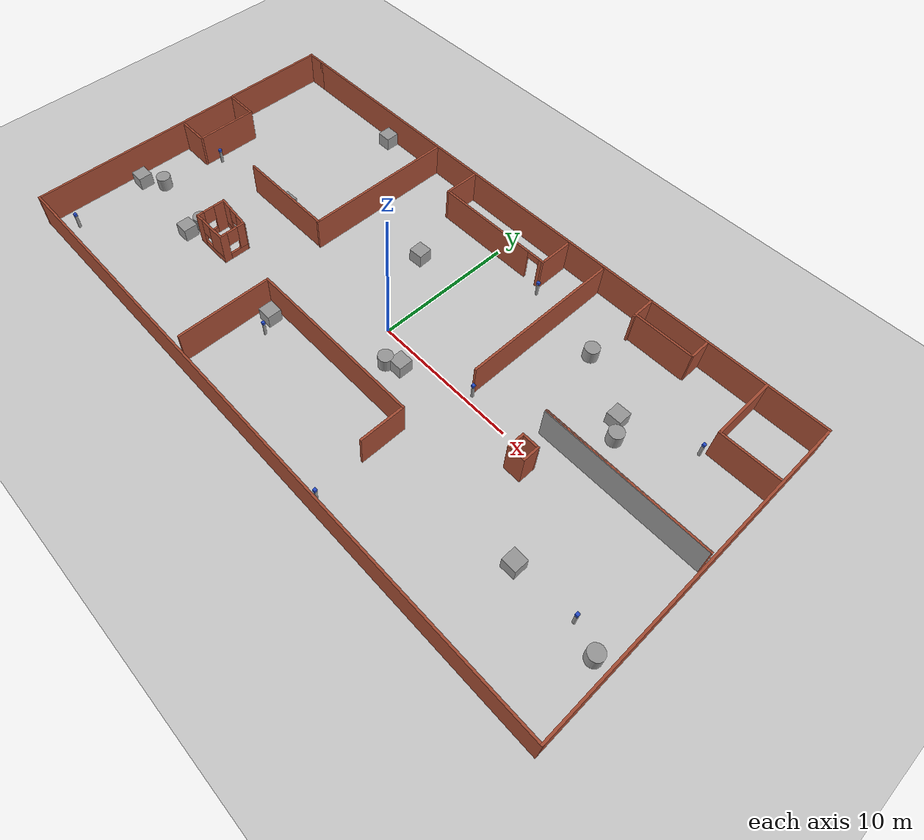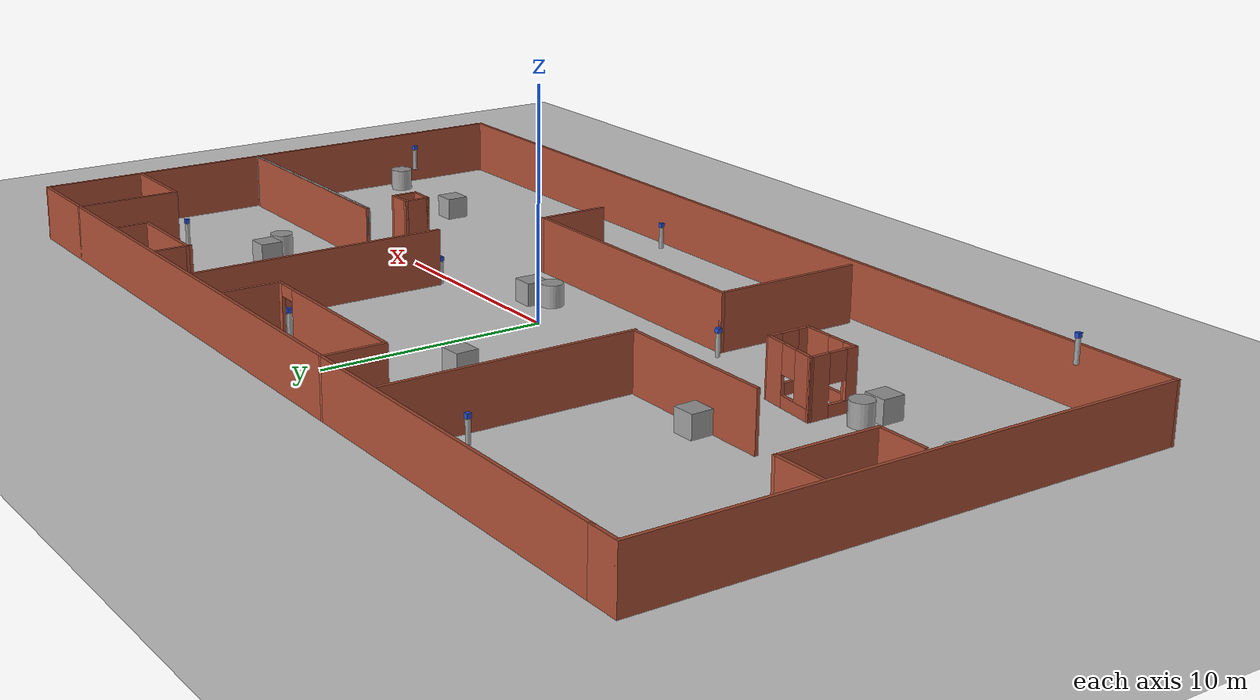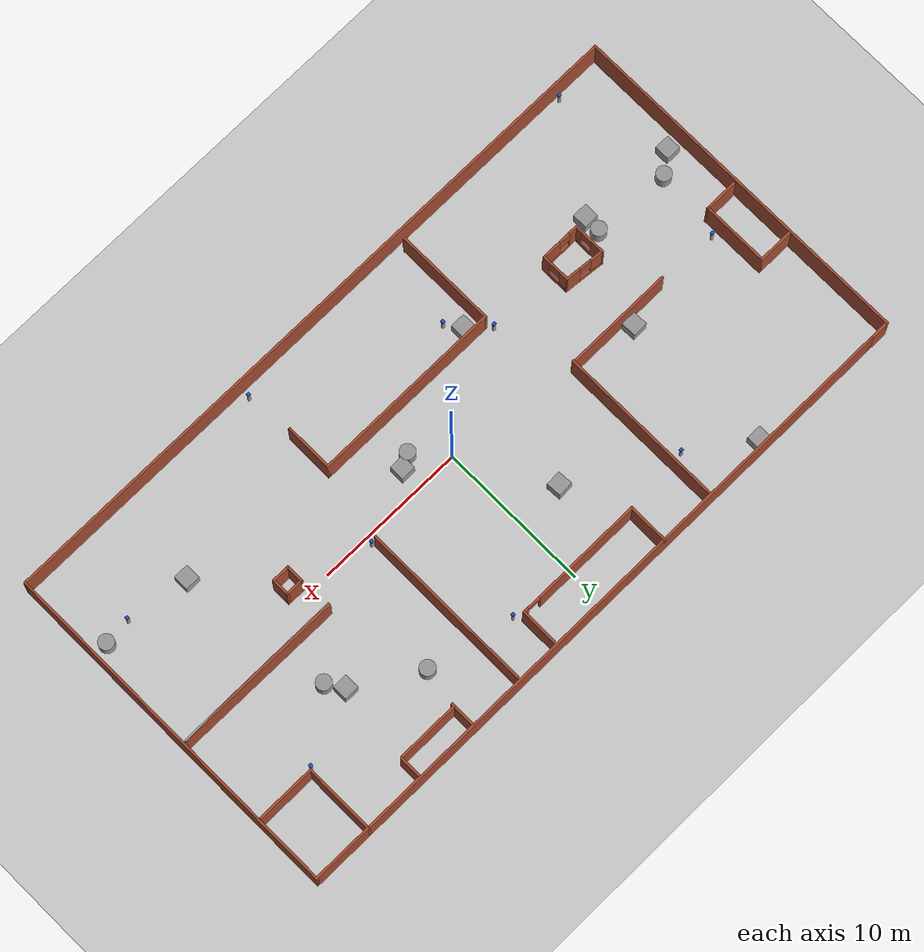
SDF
<sdf version="1.7">
 <world name="simulate_indoor">
  <model name="ground_plane">
   <static>1</static>
   <link name="link">
    <collision name="collision">
     <geometry><plane><normal>0 0 1</normal><size>100 100</size></plane></geometry>
     <surface>
      <contact><collide_bitmask>65535</collide_bitmask></contact>
      <friction><ode><mu>100</mu><mu2>50</mu2></ode></friction>
     </surface>
    </collision>
    <visual name="visual">
     <cast_shadows>0</cast_shadows>
     <geometry><plane><normal>0 0 1</normal><size>100 100</size></plane></geometry>
     <material>
      <script><uri>file://media/materials/scripts/gazebo.material</uri><name>Gazebo/Grey</name></script>
     </material>
    </visual>
   </link>
  </model>
  <gravity>0 0 -9.8</gravity>
  <magnetic_field>6e-06 2.3e-05 -4.2e-05</magnetic_field>
  <atmosphere type="adiabatic"/>
  <physics name="default_physics" default="0" type="ode">
   <max_step_size>0.001</max_step_size>
   <real_time_factor>1</real_time_factor>
   <real_time_update_rate>1000</real_time_update_rate>
  </physics>
  <scene><ambient>0.4 0.4 0.4 1</ambient><background>0.7 0.7 0.7 1</background><shadows>1</shadows></scene>
  <audio><device>default</device></audio>
  <spherical_coordinates>
   <surface_model>EARTH_WGS84</surface_model>
   <latitude_deg>0</latitude_deg>
   <longitude_deg>0</longitude_deg>
   <elevation>0</elevation>
   <heading_deg>0</heading_deg>
  </spherical_coordinates>
  <model name="building_3">
   <pose>-0.060718 0.5346 0 0 -0 0</pose>
   <link name="Wall_0">
    <collision name="Wall_0_Collision">
     <geometry><box><size>44.5 0.15 2.5</size></box></geometry>
     <pose>0 0 1.25 0 -0 0</pose>
    </collision>
    <visual name="Wall_0_Visual">
     <pose>0 0 1.25 0 -0 0</pose>
     <geometry><box><size>44.5 0.15 2.5</size></box></geometry>
     <material>
      <script><uri>file://media/materials/scripts/gazebo.material</uri><name>Gazebo/Bricks</name></script>
      <ambient>1 1 1 1</ambient>
     </material>
     <meta><layer>0</layer></meta>
    </visual>
    <pose>0.624999 11.8 0 0 -0 0</pose>
   </link>
   <link name="Wall_1">
    <collision name="Wall_1_Collision">
     <geometry><box><size>23.75 0.15 2.5</size></box></geometry>
     <pose>0 0 1.25 0 -0 0</pose>
    </collision>
    <visual name="Wall_1_Visual">
     <pose>0 0 1.25 0 -0 0</pose>
     <geometry><box><size>23.75 0.15 2.5</size></box></geometry>
     <material>
      <script><uri>file://media/materials/scripts/gazebo.material</uri><name>Gazebo/Bricks</name></script>
      <ambient>1 1 1 1</ambient>
     </material>
     <meta><layer>0</layer></meta>
    </visual>
    <pose>22.8 0 0 0 -0 -1.5708</pose>
   </link>
   <link name="Wall_10">
    <collision name="Wall_10_Collision">
     <geometry><box><size>2.5 0.15 2.5</size></box></geometry>
     <pose>0 0 1.25 0 -0 0</pose>
    </collision>
    <visual name="Wall_10_Visual">
     <pose>0 0 1.25 0 -0 0</pose>
     <geometry><box><size>2.5 0.15 2.5</size></box></geometry>
     <material>
      <script><uri>file://media/materials/scripts/gazebo.material</uri><name>Gazebo/Bricks</name></script>
      <ambient>1 1 1 1</ambient>
     </material>
     <meta><layer>0</layer></meta>
    </visual>
    <pose>3.95679 10.375 0 0 -0 1.5708</pose>
   </link>
   <link name="Wall_17">
    <collision name="Wall_17_Collision">
     <geometry><box><size>4.75 0.15 2.5</size></box></geometry>
     <pose>0 0 1.25 0 -0 0</pose>
    </collision>
    <visual name="Wall_17_Visual">
     <pose>0 0 1.25 0 -0 0</pose>
     <geometry><box><size>4.75 0.15 2.5</size></box></geometry>
     <material>
      <script><uri>file://media/materials/scripts/gazebo.material</uri><name>Gazebo/Bricks</name></script>
      <ambient>1 1 1 1</ambient>
     </material>
     <meta><layer>0</layer></meta>
    </visual>
    <pose>18.7909 9.5 0 0 -0 -1.5708</pose>
   </link>
   <link name="Wall_18">
    <collision name="Wall_18_Collision">
     <geometry><box><size>4 0.15 2.5</size></box></geometry>
     <pose>0 0 1.25 0 -0 0</pose>
    </collision>
    <visual name="Wall_18_Visual">
     <pose>0 0 1.25 0 -0 0</pose>
     <geometry><box><size>4 0.15 2.5</size></box></geometry>
     <material>
      <script><uri>file://media/materials/scripts/gazebo.material</uri><name>Gazebo/Bricks</name></script>
      <ambient>1 1 1 1</ambient>
     </material>
     <meta><layer>0</layer></meta>
    </visual>
    <pose>20.7159 7.2 0 0 -0 0</pose>
   </link>
   <link name="Wall_2">
    <collision name="Wall_2_Collision">
     <geometry><box><size>45.75 0.15 2.5</size></box></geometry>
     <pose>0 0 1.25 0 -0 0</pose>
    </collision>
    <visual name="Wall_2_Visual">
     <pose>0 0 1.25 0 -0 0</pose>
     <geometry><box><size>45.75 0.15 2.5</size></box></geometry>
     <material>
      <script><uri>file://media/materials/scripts/gazebo.material</uri><name>Gazebo/Bricks</name></script>
      <ambient>1 1 1 1</ambient>
     </material>
     <meta><layer>0</layer></meta>
    </visual>
    <pose>-1e-06 -11.8 0 0 -0 3.14159</pose>
   </link>
   <link name="Wall_20">
    <pose>-14.2202 -3.74918 0 0 -0 -1.5708</pose>
    <visual name="Wall_20_Visual_0">
     <pose>-0.663415 0 1.25 0 -0 0</pose>
     <geometry><box><size>0.92317 0.15 2.5</size></box></geometry>
     <material>
      <script><uri>file://media/materials/scripts/gazebo.material</uri><name>Gazebo/Bricks</name></script>
      <ambient>1 1 1 1</ambient>
     </material>
     <meta><layer>0</layer></meta>
    </visual>
    <collision name="Wall_20_Collision_0">
     <geometry><box><size>0.92317 0.15 2.5</size></box></geometry>
     <pose>-0.663415 0 1.25 0 -0 0</pose>
    </collision>
    <visual name="Wall_20_Visual_1">
     <pose>0.461585 0 0.25 0 -0 0</pose>
     <geometry><box><size>1.32683 0.15 0.5</size></box></geometry>
     <material>
      <script><uri>file://media/materials/scripts/gazebo.material</uri><name>Gazebo/Bricks</name></script>
      <ambient>1 1 1 1</ambient>
     </material>
     <meta><layer>0</layer></meta>
    </visual>
    <collision name="Wall_20_Collision_1">
     <geometry><box><size>1.32683 0.15 0.5</size></box></geometry>
     <pose>0.461585 0 0.25 0 -0 0</pose>
    </collision>
    <visual name="Wall_20_Visual_2">
     <pose>0.861585 0 1.5 0 -0 0</pose>
     <geometry><box><size>0.52683 0.15 2</size></box></geometry>
     <material>
      <script><uri>file://media/materials/scripts/gazebo.material</uri><name>Gazebo/Bricks</name></script>
      <ambient>1 1 1 1</ambient>
     </material>
     <meta><layer>0</layer></meta>
    </visual>
    <collision name="Wall_20_Collision_2">
     <geometry><box><size>0.52683 0.15 2</size></box></geometry>
     <pose>0.861585 0 1.5 0 -0 0</pose>
    </collision>
    <visual name="Wall_20_Visual_3">
     <pose>0.19817 0 1.9 0 -0 0</pose>
     <geometry><box><size>0.8 0.15 1.2</size></box></geometry>
     <material>
      <script><uri>file://media/materials/scripts/gazebo.material</uri><name>Gazebo/Bricks</name></script>
      <ambient>1 1 1 1</ambient>
     </material>
     <meta><layer>0</layer></meta>
    </visual>
    <collision name="Wall_20_Collision_3">
     <geometry><box><size>0.8 0.15 1.2</size></box></geometry>
     <pose>0.19817 0 1.9 0 -0 0</pose>
    </collision>
   </link>
   <link name="Wall_21">
    <pose>-12.9202 -4.79918 0 0 -0 0</pose>
    <visual name="Wall_21_Visual_0">
     <pose>-1.04504 0 1.25 0 -0 0</pose>
     <geometry><box><size>0.659914 0.15 2.5</size></box></geometry>
     <material>
      <script><uri>file://media/materials/scripts/gazebo.material</uri><name>Gazebo/Bricks</name></script>
      <ambient>1 1 1 1</ambient>
     </material>
     <meta><layer>0</layer></meta>
    </visual>
    <collision name="Wall_21_Collision_0">
     <geometry><box><size>0.659914 0.15 2.5</size></box></geometry>
     <pose>-1.04504 0 1.25 0 -0 0</pose>
    </collision>
    <visual name="Wall_21_Visual_1">
     <pose>0.329957 0 0.25 0 -0 0</pose>
     <geometry><box><size>2.09009 0.15 0.5</size></box></geometry>
     <material>
      <script><uri>file://media/materials/scripts/gazebo.material</uri><name>Gazebo/Bricks</name></script>
      <ambient>1 1 1 1</ambient>
     </material>
     <meta><layer>0</layer></meta>
    </visual>
    <collision name="Wall_21_Collision_1">
     <geometry><box><size>2.09009 0.15 0.5</size></box></geometry>
     <pose>0.329957 0 0.25 0 -0 0</pose>
    </collision>
    <visual name="Wall_21_Visual_2">
     <pose>0.729957 0 1.5 0 -0 0</pose>
     <geometry><box><size>1.29009 0.15 2</size></box></geometry>
     <material>
      <script><uri>file://media/materials/scripts/gazebo.material</uri><name>Gazebo/Bricks</name></script>
      <ambient>1 1 1 1</ambient>
     </material>
     <meta><layer>0</layer></meta>
    </visual>
    <collision name="Wall_21_Collision_2">
     <geometry><box><size>1.29009 0.15 2</size></box></geometry>
     <pose>0.729957 0 1.5 0 -0 0</pose>
    </collision>
    <visual name="Wall_21_Visual_3">
     <pose>-0.315086 0 1.9 0 -0 0</pose>
     <geometry><box><size>0.8 0.15 1.2</size></box></geometry>
     <material>
      <script><uri>file://media/materials/scripts/gazebo.material</uri><name>Gazebo/Bricks</name></script>
      <ambient>1 1 1 1</ambient>
     </material>
     <meta><layer>0</layer></meta>
    </visual>
    <collision name="Wall_21_Collision_3">
     <geometry><box><size>0.8 0.15 1.2</size></box></geometry>
     <pose>-0.315086 0 1.9 0 -0 0</pose>
    </collision>
   </link>
   <link name="Wall_22">
    <pose>-11.6202 -3.87418 0 0 -0 1.5708</pose>
    <visual name="Wall_22_Visual_0">
     <pose>-0.715325 0 1.25 0 -0 0</pose>
     <geometry><box><size>0.569349 0.15 2.5</size></box></geometry>
     <material>
      <script><uri>file://media/materials/scripts/gazebo.material</uri><name>Gazebo/Bricks</name></script>
      <ambient>1 1 1 1</ambient>
     </material>
     <meta><layer>0</layer></meta>
    </visual>
    <collision name="Wall_22_Collision_0">
     <geometry><box><size>0.569349 0.15 2.5</size></box></geometry>
     <pose>-0.715325 0 1.25 0 -0 0</pose>
    </collision>
    <visual name="Wall_22_Visual_1">
     <pose>0.284675 0 0.25 0 -0 0</pose>
     <geometry><box><size>1.43065 0.15 0.5</size></box></geometry>
     <material>
      <script><uri>file://media/materials/scripts/gazebo.material</uri><name>Gazebo/Bricks</name></script>
      <ambient>1 1 1 1</ambient>
     </material>
     <meta><layer>0</layer></meta>
    </visual>
    <collision name="Wall_22_Collision_1">
     <geometry><box><size>1.43065 0.15 0.5</size></box></geometry>
     <pose>0.284675 0 0.25 0 -0 0</pose>
    </collision>
    <visual name="Wall_22_Visual_2">
     <pose>0.684675 0 1.5 0 -0 0</pose>
     <geometry><box><size>0.630651 0.15 2</size></box></geometry>
     <material>
      <script><uri>file://media/materials/scripts/gazebo.material</uri><name>Gazebo/Bricks</name></script>
      <ambient>1 1 1 1</ambient>
     </material>
     <meta><layer>0</layer></meta>
    </visual>
    <collision name="Wall_22_Collision_2">
     <geometry><box><size>0.630651 0.15 2</size></box></geometry>
     <pose>0.684675 0 1.5 0 -0 0</pose>
    </collision>
    <visual name="Wall_22_Visual_3">
     <pose>-0.030651 0 1.9 0 -0 0</pose>
     <geometry><box><size>0.8 0.15 1.2</size></box></geometry>
     <material>
      <script><uri>file://media/materials/scripts/gazebo.material</uri><name>Gazebo/Bricks</name></script>
      <ambient>1 1 1 1</ambient>
     </material>
     <meta><layer>0</layer></meta>
    </visual>
    <collision name="Wall_22_Collision_3">
     <geometry><box><size>0.8 0.15 1.2</size></box></geometry>
     <pose>-0.030651 0 1.9 0 -0 0</pose>
    </collision>
   </link>
   <link name="Wall_23">
    <pose>-12.9202 -2.82418 0 0 -0 3.04573</pose>
    <visual name="Wall_23_Visual_0">
     <pose>-0.870697 0 1.25 0 -0 0</pose>
     <geometry><box><size>1.0206 0.15 2.5</size></box></geometry>
     <material>
      <script><uri>file://media/materials/scripts/gazebo.material</uri><name>Gazebo/Bricks</name></script>
      <ambient>1 1 1 1</ambient>
     </material>
     <meta><layer>0</layer></meta>
    </visual>
    <collision name="Wall_23_Collision_0">
     <geometry><box><size>1.0206 0.15 2.5</size></box></geometry>
     <pose>-0.870697 0 1.25 0 -0 0</pose>
    </collision>
    <visual name="Wall_23_Visual_1">
     <pose>0.510298 0 0.25 0 -0 0</pose>
     <geometry><box><size>1.7414 0.15 0.5</size></box></geometry>
     <material>
      <script><uri>file://media/materials/scripts/gazebo.material</uri><name>Gazebo/Bricks</name></script>
      <ambient>1 1 1 1</ambient>
     </material>
     <meta><layer>0</layer></meta>
    </visual>
    <collision name="Wall_23_Collision_1">
     <geometry><box><size>1.7414 0.15 0.5</size></box></geometry>
     <pose>0.510298 0 0.25 0 -0 0</pose>
    </collision>
    <visual name="Wall_23_Visual_2">
     <pose>0.910298 0 1.5 0 -0 0</pose>
     <geometry><box><size>0.941395 0.15 2</size></box></geometry>
     <material>
      <script><uri>file://media/materials/scripts/gazebo.material</uri><name>Gazebo/Bricks</name></script>
      <ambient>1 1 1 1</ambient>
     </material>
     <meta><layer>0</layer></meta>
    </visual>
    <collision name="Wall_23_Collision_2">
     <geometry><box><size>0.941395 0.15 2</size></box></geometry>
     <pose>0.910298 0 1.5 0 -0 0</pose>
    </collision>
    <visual name="Wall_23_Visual_3">
     <pose>0.039601 0 1.9 0 -0 0</pose>
     <geometry><box><size>0.8 0.15 1.2</size></box></geometry>
     <material>
      <script><uri>file://media/materials/scripts/gazebo.material</uri><name>Gazebo/Bricks</name></script>
      <ambient>1 1 1 1</ambient>
     </material>
     <meta><layer>0</layer></meta>
    </visual>
    <collision name="Wall_23_Collision_3">
     <geometry><box><size>0.8 0.15 1.2</size></box></geometry>
     <pose>0.039601 0 1.9 0 -0 0</pose>
    </collision>
   </link>
   <link name="Wall_25">
    <collision name="Wall_25_Collision">
     <geometry><box><size>1.25 0.15 2.5</size></box></geometry>
     <pose>0 0 1.25 0 -0 0</pose>
    </collision>
    <visual name="Wall_25_Visual">
     <pose>0 0 1.25 0 -0 0</pose>
     <geometry><box><size>1.25 0.15 2.5</size></box></geometry>
     <material>
      <script><uri>file://media/materials/scripts/gazebo.material</uri><name>Gazebo/Bricks</name></script>
      <ambient>1 1 1 1</ambient>
     </material>
     <meta><layer>0</layer></meta>
    </visual>
    <pose>11.6215 -1.48359 0 0 -0 -1.5708</pose>
   </link>
   <link name="Wall_26">
    <collision name="Wall_26_Collision">
     <geometry><box><size>1.25 0.15 2.5</size></box></geometry>
     <pose>0 0 1.25 0 -0 0</pose>
    </collision>
    <visual name="Wall_26_Visual">
     <pose>0 0 1.25 0 -0 0</pose>
     <geometry><box><size>1.25 0.15 2.5</size></box></geometry>
     <material>
      <script><uri>file://media/materials/scripts/gazebo.material</uri><name>Gazebo/Bricks</name></script>
      <ambient>1 1 1 1</ambient>
     </material>
     <meta><layer>0</layer></meta>
    </visual>
    <pose>12.1715 -2.0336 0 0 -0 0</pose>
   </link>
   <link name="Wall_27">
    <collision name="Wall_27_Collision">
     <geometry><box><size>1.25 0.15 2.5</size></box></geometry>
     <pose>0 0 1.25 0 -0 0</pose>
    </collision>
    <visual name="Wall_27_Visual">
     <pose>0 0 1.25 0 -0 0</pose>
     <geometry><box><size>1.25 0.15 2.5</size></box></geometry>
     <material>
      <script><uri>file://media/materials/scripts/gazebo.material</uri><name>Gazebo/Bricks</name></script>
      <ambient>1 1 1 1</ambient>
     </material>
     <meta><layer>0</layer></meta>
    </visual>
    <pose>12.7215 -1.48359 0 0 -0 1.5708</pose>
   </link>
   <link name="Wall_28">
    <collision name="Wall_28_Collision">
     <geometry><box><size>1.25 0.15 2.5</size></box></geometry>
     <pose>0 0 1.25 0 -0 0</pose>
    </collision>
    <visual name="Wall_28_Visual">
     <pose>0 0 1.25 0 -0 0</pose>
     <geometry><box><size>1.25 0.15 2.5</size></box></geometry>
     <material>
      <script><uri>file://media/materials/scripts/gazebo.material</uri><name>Gazebo/Bricks</name></script>
      <ambient>1 1 1 1</ambient>
     </material>
     <meta><layer>0</layer></meta>
    </visual>
    <pose>12.1715 -0.933595 0 0 -0 3.14159</pose>
   </link>
   <link name="Wall_3">
    <collision name="Wall_3_Collision">
     <geometry><box><size>23.75 0.15 2.5</size></box></geometry>
     <pose>0 0 1.25 0 -0 0</pose>
    </collision>
    <visual name="Wall_3_Visual">
     <pose>0 0 1.25 0 -0 0</pose>
     <geometry><box><size>23.75 0.15 2.5</size></box></geometry>
     <material>
      <script><uri>file://media/materials/scripts/gazebo.material</uri><name>Gazebo/Bricks</name></script>
      <ambient>1 1 1 1</ambient>
     </material>
     <meta><layer>0</layer></meta>
    </visual>
    <pose>-22.8 0 0 0 -0 1.5708</pose>
   </link>
   <link name="Wall_4">
    <collision name="Wall_4_Collision">
     <geometry><box><size>1.5 0.15 2.5</size></box></geometry>
     <pose>0 0 1.25 0 -0 0</pose>
    </collision>
    <visual name="Wall_4_Visual">
     <pose>0 0 1.25 0 -0 0</pose>
     <geometry><box><size>1.5 0.15 2.5</size></box></geometry>
     <material>
      <script><uri>file://media/materials/scripts/gazebo.material</uri><name>Gazebo/Bricks</name></script>
      <ambient>1 1 1 1</ambient>
     </material>
     <meta><layer>0</layer></meta>
    </visual>
    <pose>-22.125 11.8 0 0 -0 0</pose>
   </link>
   <link name="Wall_8">
    <collision name="Wall_8_Collision">
     <geometry><box><size>2.75 0.15 2.5</size></box></geometry>
     <pose>0 0 1.25 0 -0 0</pose>
    </collision>
    <visual name="Wall_8_Visual">
     <pose>0 0 1.25 0 -0 0</pose>
     <geometry><box><size>2.75 0.15 2.5</size></box></geometry>
     <material>
      <script><uri>file://media/materials/scripts/gazebo.material</uri><name>Gazebo/Bricks</name></script>
      <ambient>1 1 1 1</ambient>
     </material>
     <meta><layer>0</layer></meta>
    </visual>
    <pose>-4.64321 10.5 0 0 -0 -1.5708</pose>
   </link>
   <link name="Wall_9">
    <pose>-0.343211 9.2 0 0 -0 0</pose>
    <visual name="Wall_9_Visual_0">
     <pose>-0.647828 0 1.25 0 -0 0</pose>
     <geometry><box><size>7.45434 0.15 2.5</size></box></geometry>
     <material>
      <script><uri>file://media/materials/scripts/gazebo.material</uri><name>Gazebo/Bricks</name></script>
      <ambient>1 1 1 1</ambient>
     </material>
     <meta><layer>0</layer></meta>
    </visual>
    <collision name="Wall_9_Collision_0">
     <geometry><box><size>7.45434 0.15 2.5</size></box></geometry>
     <pose>-0.647828 0 1.25 0 -0 0</pose>
    </collision>
    <visual name="Wall_9_Visual_1">
     <pose>4.17717 0 1.25 0 -0 0</pose>
     <geometry><box><size>0.395657 0.15 2.5</size></box></geometry>
     <material>
      <script><uri>file://media/materials/scripts/gazebo.material</uri><name>Gazebo/Bricks</name></script>
      <ambient>1 1 1 1</ambient>
     </material>
     <meta><layer>0</layer></meta>
    </visual>
    <collision name="Wall_9_Collision_1">
     <geometry><box><size>0.395657 0.15 2.5</size></box></geometry>
     <pose>4.17717 0 1.25 0 -0 0</pose>
    </collision>
    <visual name="Wall_9_Visual_2">
     <pose>3.52934 0 2.25 0 -0 0</pose>
     <geometry><box><size>0.9 0.15 0.5</size></box></geometry>
     <material>
      <script><uri>file://media/materials/scripts/gazebo.material</uri><name>Gazebo/Bricks</name></script>
      <ambient>1 1 1 1</ambient>
     </material>
     <meta><layer>0</layer></meta>
    </visual>
    <collision name="Wall_9_Collision_2">
     <geometry><box><size>0.9 0.15 0.5</size></box></geometry>
     <pose>3.52934 0 2.25 0 -0 0</pose>
    </collision>
   </link>
   <static>1</static>
  </model>
  <model name="UWB_0">
   <link name="link_1">
    <inertial>
     <mass>1</mass>
     <inertia><ixx>0.145833</ixx><ixy>0</ixy><ixz>0</ixz><iyy>0.145833</iyy><iyz>0</iyz><izz>0.125</izz></inertia>
    </inertial>
    <pose>0 0 0.5 0 -0 0</pose>
    <visual name="visual">
     <geometry><cylinder><radius>0.1</radius><length>1</length></cylinder></geometry>
     <material>
      <lighting>1</lighting>
      <script><uri>file://media/materials/scripts/gazebo.material</uri><name>Gazebo/Grey</name></script>
     </material>
    </visual>
    <collision name="collision">
     <geometry><cylinder><radius>0.1</radius><length>1</length></cylinder></geometry>
     <surface>
      <friction>
       <ode><mu>1</mu><mu2>1</mu2><fdir1>0 0 0</fdir1><slip1>0</slip1><slip2>0</slip2></ode>
       <torsional>
        <coefficient>1</coefficient>
        <patch_radius>0</patch_radius>
        <surface_radius>0</surface_radius>
        <use_patch_radius>1</use_patch_radius>
        <ode><slip>0</slip></ode>
       </torsional>
      </friction>
      <bounce><restitution_coefficient>0</restitution_coefficient><threshold>1e+06</threshold></bounce>
      <contact>
       <collide_without_contact>0</collide_without_contact>
       <collide_without_contact_bitmask>1</collide_without_contact_bitmask>
       <collide_bitmask>1</collide_bitmask>
       <ode>
        <soft_cfm>0</soft_cfm>
        <soft_erp>0.2</soft_erp>
        <kp>1e+13</kp>
        <kd>1</kd>
        <max_vel>0.01</max_vel>
        <min_depth>0</min_depth>
       </ode>
       <bullet>
        <split_impulse>1</split_impulse>
        <split_impulse_penetration_threshold>-0.01</split_impulse_penetration_threshold>
        <soft_cfm>0</soft_cfm>
        <soft_erp>0.2</soft_erp>
        <kp>1e+13</kp>
        <kd>1</kd>
       </bullet>
      </contact>
     </surface>
    </collision>
   </link>
   <link name="link_2">
    <inertial>
     <mass>1</mass>
     <inertia>
      <ixx>0.166667</ixx>
      <ixy>0</ixy>
      <ixz>0</ixz>
      <iyy>0.166667</iyy>
      <iyz>0</iyz>
      <izz>0.166667</izz>
     </inertia>
    </inertial>
    <pose>0 0 1.1 0 -0 0</pose>
    <visual name="visual">
     <geometry><box><size>0.2 0.2 0.2</size></box></geometry>
     <material>
      <lighting>1</lighting>
      <script><uri>file://media/materials/scripts/gazebo.material</uri><name>Gazebo/Blue</name></script>
      <shader type="vertex"><normal_map>__default__</normal_map></shader>
     </material>
    </visual>
    <collision name="collision">
     <geometry><box><size>0.2 0.2 0.2</size></box></geometry>
     <surface>
      <friction>
       <ode><mu>1</mu><mu2>1</mu2><fdir1>0 0 0</fdir1><slip1>0</slip1><slip2>0</slip2></ode>
       <torsional>
        <coefficient>1</coefficient>
        <patch_radius>0</patch_radius>
        <surface_radius>0</surface_radius>
        <use_patch_radius>1</use_patch_radius>
        <ode><slip>0</slip></ode>
       </torsional>
      </friction>
      <bounce><restitution_coefficient>0</restitution_coefficient><threshold>1e+06</threshold></bounce>
      <contact>
       <collide_without_contact>0</collide_without_contact>
       <collide_without_contact_bitmask>1</collide_without_contact_bitmask>
       <collide_bitmask>1</collide_bitmask>
       <ode>
        <soft_cfm>0</soft_cfm>
        <soft_erp>0.2</soft_erp>
        <kp>1e+13</kp>
        <kd>1</kd>
        <max_vel>0.01</max_vel>
        <min_depth>0</min_depth>
       </ode>
       <bullet>
        <split_impulse>1</split_impulse>
        <split_impulse_penetration_threshold>-0.01</split_impulse_penetration_threshold>
        <soft_cfm>0</soft_cfm>
        <soft_erp>0.2</soft_erp>
        <kp>1e+13</kp>
        <kd>1</kd>
       </bullet>
      </contact>
     </surface>
    </collision>
   </link>
   <static>1</static>
   <pose>-19.0705 -10.4583 2.04937 0 -0 0</pose>
  </model>
  <model name="UWB_1">
   <link name="link_1">
    <inertial>
     <mass>1</mass>
     <inertia><ixx>0.145833</ixx><ixy>0</ixy><ixz>0</ixz><iyy>0.145833</iyy><iyz>0</iyz><izz>0.125</izz></inertia>
    </inertial>
    <pose>0 0 0.5 0 -0 0</pose>
    <visual name="visual">
     <geometry><cylinder><radius>0.1</radius><length>1</length></cylinder></geometry>
     <material>
      <lighting>1</lighting>
      <script><uri>file://media/materials/scripts/gazebo.material</uri><name>Gazebo/Grey</name></script>
     </material>
    </visual>
    <collision name="collision">
     <geometry><cylinder><radius>0.1</radius><length>1</length></cylinder></geometry>
     <surface>
      <friction>
       <ode><mu>1</mu><mu2>1</mu2><fdir1>0 0 0</fdir1><slip1>0</slip1><slip2>0</slip2></ode>
       <torsional>
        <coefficient>1</coefficient>
        <patch_radius>0</patch_radius>
        <surface_radius>0</surface_radius>
        <use_patch_radius>1</use_patch_radius>
        <ode><slip>0</slip></ode>
       </torsional>
      </friction>
      <bounce><restitution_coefficient>0</restitution_coefficient><threshold>1e+06</threshold></bounce>
      <contact>
       <collide_without_contact>0</collide_without_contact>
       <collide_without_contact_bitmask>1</collide_without_contact_bitmask>
       <collide_bitmask>1</collide_bitmask>
       <ode>
        <soft_cfm>0</soft_cfm>
        <soft_erp>0.2</soft_erp>
        <kp>1e+13</kp>
        <kd>1</kd>
        <max_vel>0.01</max_vel>
        <min_depth>0</min_depth>
       </ode>
       <bullet>
        <split_impulse>1</split_impulse>
        <split_impulse_penetration_threshold>-0.01</split_impulse_penetration_threshold>
        <soft_cfm>0</soft_cfm>
        <soft_erp>0.2</soft_erp>
        <kp>1e+13</kp>
        <kd>1</kd>
       </bullet>
      </contact>
     </surface>
    </collision>
   </link>
   <link name="link_2">
    <inertial>
     <mass>1</mass>
     <inertia>
      <ixx>0.166667</ixx>
      <ixy>0</ixy>
      <ixz>0</ixz>
      <iyy>0.166667</iyy>
      <iyz>0</iyz>
      <izz>0.166667</izz>
     </inertia>
    </inertial>
    <pose>0 0 1.1 0 -0 0</pose>
    <visual name="visual">
     <geometry><box><size>0.2 0.2 0.2</size></box></geometry>
     <material>
      <lighting>1</lighting>
      <script><uri>file://media/materials/scripts/gazebo.material</uri><name>Gazebo/Blue</name></script>
      <shader type="vertex"><normal_map>__default__</normal_map></shader>
     </material>
    </visual>
    <collision name="collision">
     <geometry><box><size>0.2 0.2 0.2</size></box></geometry>
     <surface>
      <friction>
       <ode><mu>1</mu><mu2>1</mu2><fdir1>0 0 0</fdir1><slip1>0</slip1><slip2>0</slip2></ode>
       <torsional>
        <coefficient>1</coefficient>
        <patch_radius>0</patch_radius>
        <surface_radius>0</surface_radius>
        <use_patch_radius>1</use_patch_radius>
        <ode><slip>0</slip></ode>
       </torsional>
      </friction>
      <bounce><restitution_coefficient>0</restitution_coefficient><threshold>1e+06</threshold></bounce>
      <contact>
       <collide_without_contact>0</collide_without_contact>
       <collide_without_contact_bitmask>1</collide_without_contact_bitmask>
       <collide_bitmask>1</collide_bitmask>
       <ode>
        <soft_cfm>0</soft_cfm>
        <soft_erp>0.2</soft_erp>
        <kp>1e+13</kp>
        <kd>1</kd>
        <max_vel>0.01</max_vel>
        <min_depth>0</min_depth>
       </ode>
       <bullet>
        <split_impulse>1</split_impulse>
        <split_impulse_penetration_threshold>-0.01</split_impulse_penetration_threshold>
        <soft_cfm>0</soft_cfm>
        <soft_erp>0.2</soft_erp>
        <kp>1e+13</kp>
        <kd>1</kd>
       </bullet>
      </contact>
     </surface>
    </collision>
   </link>
   <static>1</static>
   <pose>20.0355 -5.74231 1.38234 0 -0 0</pose>
  </model>
  <model name="UWB_2">
   <link name="link_1">
    <inertial>
     <mass>1</mass>
     <inertia><ixx>0.145833</ixx><ixy>0</ixy><ixz>0</ixz><iyy>0.145833</iyy><iyz>0</iyz><izz>0.125</izz></inertia>
    </inertial>
    <pose>0 0 0.5 0 -0 0</pose>
    <visual name="visual">
     <geometry><cylinder><radius>0.1</radius><length>1</length></cylinder></geometry>
     <material>
      <lighting>1</lighting>
      <script><uri>file://media/materials/scripts/gazebo.material</uri><name>Gazebo/Grey</name></script>
     </material>
    </visual>
    <collision name="collision">
     <geometry><cylinder><radius>0.1</radius><length>1</length></cylinder></geometry>
     <surface>
      <friction>
       <ode><mu>1</mu><mu2>1</mu2><fdir1>0 0 0</fdir1><slip1>0</slip1><slip2>0</slip2></ode>
       <torsional>
        <coefficient>1</coefficient>
        <patch_radius>0</patch_radius>
        <surface_radius>0</surface_radius>
        <use_patch_radius>1</use_patch_radius>
        <ode><slip>0</slip></ode>
       </torsional>
      </friction>
      <bounce><restitution_coefficient>0</restitution_coefficient><threshold>1e+06</threshold></bounce>
      <contact>
       <collide_without_contact>0</collide_without_contact>
       <collide_without_contact_bitmask>1</collide_without_contact_bitmask>
       <collide_bitmask>1</collide_bitmask>
       <ode>
        <soft_cfm>0</soft_cfm>
        <soft_erp>0.2</soft_erp>
        <kp>1e+13</kp>
        <kd>1</kd>
        <max_vel>0.01</max_vel>
        <min_depth>0</min_depth>
       </ode>
       <bullet>
        <split_impulse>1</split_impulse>
        <split_impulse_penetration_threshold>-0.01</split_impulse_penetration_threshold>
        <soft_cfm>0</soft_cfm>
        <soft_erp>0.2</soft_erp>
        <kp>1e+13</kp>
        <kd>1</kd>
       </bullet>
      </contact>
     </surface>
    </collision>
   </link>
   <link name="link_2">
    <inertial>
     <mass>1</mass>
     <inertia>
      <ixx>0.166667</ixx>
      <ixy>0</ixy>
      <ixz>0</ixz>
      <iyy>0.166667</iyy>
      <iyz>0</iyz>
      <izz>0.166667</izz>
     </inertia>
    </inertial>
    <pose>0 0 1.1 0 -0 0</pose>
    <visual name="visual">
     <geometry><box><size>0.2 0.2 0.2</size></box></geometry>
     <material>
      <lighting>1</lighting>
      <script><uri>file://media/materials/scripts/gazebo.material</uri><name>Gazebo/Blue</name></script>
      <shader type="vertex"><normal_map>__default__</normal_map></shader>
     </material>
    </visual>
    <collision name="collision">
     <geometry><box><size>0.2 0.2 0.2</size></box></geometry>
     <surface>
      <friction>
       <ode><mu>1</mu><mu2>1</mu2><fdir1>0 0 0</fdir1><slip1>0</slip1><slip2>0</slip2></ode>
       <torsional>
        <coefficient>1</coefficient>
        <patch_radius>0</patch_radius>
        <surface_radius>0</surface_radius>
        <use_patch_radius>1</use_patch_radius>
        <ode><slip>0</slip></ode>
       </torsional>
      </friction>
      <bounce><restitution_coefficient>0</restitution_coefficient><threshold>1e+06</threshold></bounce>
      <contact>
       <collide_without_contact>0</collide_without_contact>
       <collide_without_contact_bitmask>1</collide_without_contact_bitmask>
       <collide_bitmask>1</collide_bitmask>
       <ode>
        <soft_cfm>0</soft_cfm>
        <soft_erp>0.2</soft_erp>
        <kp>1e+13</kp>
        <kd>1</kd>
        <max_vel>0.01</max_vel>
        <min_depth>0</min_depth>
       </ode>
       <bullet>
        <split_impulse>1</split_impulse>
        <split_impulse_penetration_threshold>-0.01</split_impulse_penetration_threshold>
        <soft_cfm>0</soft_cfm>
        <soft_erp>0.2</soft_erp>
        <kp>1e+13</kp>
        <kd>1</kd>
       </bullet>
      </contact>
     </surface>
    </collision>
   </link>
   <static>1</static>
   <pose>4.22868 9.2032 0 0 -0 0</pose>
  </model>
  <model name="UWB_3">
   <link name="link_1">
    <inertial>
     <mass>1</mass>
     <inertia><ixx>0.145833</ixx><ixy>0</ixy><ixz>0</ixz><iyy>0.145833</iyy><iyz>0</iyz><izz>0.125</izz></inertia>
    </inertial>
    <pose>0 0 0.5 0 -0 0</pose>
    <visual name="visual">
     <geometry><cylinder><radius>0.1</radius><length>1</length></cylinder></geometry>
     <material>
      <lighting>1</lighting>
      <script><uri>file://media/materials/scripts/gazebo.material</uri><name>Gazebo/Grey</name></script>
     </material>
    </visual>
    <collision name="collision">
     <geometry><cylinder><radius>0.1</radius><length>1</length></cylinder></geometry>
     <surface>
      <friction>
       <ode><mu>1</mu><mu2>1</mu2><fdir1>0 0 0</fdir1><slip1>0</slip1><slip2>0</slip2></ode>
       <torsional>
        <coefficient>1</coefficient>
        <patch_radius>0</patch_radius>
        <surface_radius>0</surface_radius>
        <use_patch_radius>1</use_patch_radius>
        <ode><slip>0</slip></ode>
       </torsional>
      </friction>
      <bounce><restitution_coefficient>0</restitution_coefficient><threshold>1e+06</threshold></bounce>
      <contact>
       <collide_without_contact>0</collide_without_contact>
       <collide_without_contact_bitmask>1</collide_without_contact_bitmask>
       <collide_bitmask>1</collide_bitmask>
       <ode>
        <soft_cfm>0</soft_cfm>
        <soft_erp>0.2</soft_erp>
        <kp>1e+13</kp>
        <kd>1</kd>
        <max_vel>0.01</max_vel>
        <min_depth>0</min_depth>
       </ode>
       <bullet>
        <split_impulse>1</split_impulse>
        <split_impulse_penetration_threshold>-0.01</split_impulse_penetration_threshold>
        <soft_cfm>0</soft_cfm>
        <soft_erp>0.2</soft_erp>
        <kp>1e+13</kp>
        <kd>1</kd>
       </bullet>
      </contact>
     </surface>
    </collision>
   </link>
   <link name="link_2">
    <inertial>
     <mass>1</mass>
     <inertia>
      <ixx>0.166667</ixx>
      <ixy>0</ixy>
      <ixz>0</ixz>
      <iyy>0.166667</iyy>
      <iyz>0</iyz>
      <izz>0.166667</izz>
     </inertia>
    </inertial>
    <pose>0 0 1.1 0 -0 0</pose>
    <visual name="visual">
     <geometry><box><size>0.2 0.2 0.2</size></box></geometry>
     <material>
      <lighting>1</lighting>
      <script><uri>file://media/materials/scripts/gazebo.material</uri><name>Gazebo/Blue</name></script>
      <shader type="vertex"><normal_map>__default__</normal_map></shader>
     </material>
    </visual>
    <collision name="collision">
     <geometry><box><size>0.2 0.2 0.2</size></box></geometry>
     <surface>
      <friction>
       <ode><mu>1</mu><mu2>1</mu2><fdir1>0 0 0</fdir1><slip1>0</slip1><slip2>0</slip2></ode>
       <torsional>
        <coefficient>1</coefficient>
        <patch_radius>0</patch_radius>
        <surface_radius>0</surface_radius>
        <use_patch_radius>1</use_patch_radius>
        <ode><slip>0</slip></ode>
       </torsional>
      </friction>
      <bounce><restitution_coefficient>0</restitution_coefficient><threshold>1e+06</threshold></bounce>
      <contact>
       <collide_without_contact>0</collide_without_contact>
       <collide_without_contact_bitmask>1</collide_without_contact_bitmask>
       <collide_bitmask>1</collide_bitmask>
       <ode>
        <soft_cfm>0</soft_cfm>
        <soft_erp>0.2</soft_erp>
        <kp>1e+13</kp>
        <kd>1</kd>
        <max_vel>0.01</max_vel>
        <min_depth>0</min_depth>
       </ode>
       <bullet>
        <split_impulse>1</split_impulse>
        <split_impulse_penetration_threshold>-0.01</split_impulse_penetration_threshold>
        <soft_cfm>0</soft_cfm>
        <soft_erp>0.2</soft_erp>
        <kp>1e+13</kp>
        <kd>1</kd>
       </bullet>
      </contact>
     </surface>
    </collision>
   </link>
   <static>1</static>
   <pose>-19.9487 1.28309 0 0 -0 0</pose>
  </model>
  <model name="UWB_4">
   <link name="link_1">
    <inertial>
     <mass>1</mass>
     <inertia><ixx>0.145833</ixx><ixy>0</ixy><ixz>0</ixz><iyy>0.145833</iyy><iyz>0</iyz><izz>0.125</izz></inertia>
    </inertial>
    <pose>0 0 0.5 0 -0 0</pose>
    <visual name="visual">
     <geometry><cylinder><radius>0.1</radius><length>1</length></cylinder></geometry>
     <material>
      <lighting>1</lighting>
      <script><uri>file://media/materials/scripts/gazebo.material</uri><name>Gazebo/Grey</name></script>
     </material>
    </visual>
    <collision name="collision">
     <geometry><cylinder><radius>0.1</radius><length>1</length></cylinder></geometry>
     <surface>
      <friction>
       <ode><mu>1</mu><mu2>1</mu2><fdir1>0 0 0</fdir1><slip1>0</slip1><slip2>0</slip2></ode>
       <torsional>
        <coefficient>1</coefficient>
        <patch_radius>0</patch_radius>
        <surface_radius>0</surface_radius>
        <use_patch_radius>1</use_patch_radius>
        <ode><slip>0</slip></ode>
       </torsional>
      </friction>
      <bounce><restitution_coefficient>0</restitution_coefficient><threshold>1e+06</threshold></bounce>
      <contact>
       <collide_without_contact>0</collide_without_contact>
       <collide_without_contact_bitmask>1</collide_without_contact_bitmask>
       <collide_bitmask>1</collide_bitmask>
       <ode>
        <soft_cfm>0</soft_cfm>
        <soft_erp>0.2</soft_erp>
        <kp>1e+13</kp>
        <kd>1</kd>
        <max_vel>0.01</max_vel>
        <min_depth>0</min_depth>
       </ode>
       <bullet>
        <split_impulse>1</split_impulse>
        <split_impulse_penetration_threshold>-0.01</split_impulse_penetration_threshold>
        <soft_cfm>0</soft_cfm>
        <soft_erp>0.2</soft_erp>
        <kp>1e+13</kp>
        <kd>1</kd>
       </bullet>
      </contact>
     </surface>
    </collision>
   </link>
   <link name="link_2">
    <inertial>
     <mass>1</mass>
     <inertia>
      <ixx>0.166667</ixx>
      <ixy>0</ixy>
      <ixz>0</ixz>
      <iyy>0.166667</iyy>
      <iyz>0</iyz>
      <izz>0.166667</izz>
     </inertia>
    </inertial>
    <pose>0 0 1.1 0 -0 0</pose>
    <visual name="visual">
     <geometry><box><size>0.2 0.2 0.2</size></box></geometry>
     <material>
      <lighting>1</lighting>
      <script><uri>file://media/materials/scripts/gazebo.material</uri><name>Gazebo/Blue</name></script>
      <shader type="vertex"><normal_map>__default__</normal_map></shader>
     </material>
    </visual>
    <collision name="collision">
     <geometry><box><size>0.2 0.2 0.2</size></box></geometry>
     <surface>
      <friction>
       <ode><mu>1</mu><mu2>1</mu2><fdir1>0 0 0</fdir1><slip1>0</slip1><slip2>0</slip2></ode>
       <torsional>
        <coefficient>1</coefficient>
        <patch_radius>0</patch_radius>
        <surface_radius>0</surface_radius>
        <use_patch_radius>1</use_patch_radius>
        <ode><slip>0</slip></ode>
       </torsional>
      </friction>
      <bounce><restitution_coefficient>0</restitution_coefficient><threshold>1e+06</threshold></bounce>
      <contact>
       <collide_without_contact>0</collide_without_contact>
       <collide_without_contact_bitmask>1</collide_without_contact_bitmask>
       <collide_bitmask>1</collide_bitmask>
       <ode>
        <soft_cfm>0</soft_cfm>
        <soft_erp>0.2</soft_erp>
        <kp>1e+13</kp>
        <kd>1</kd>
        <max_vel>0.01</max_vel>
        <min_depth>0</min_depth>
       </ode>
       <bullet>
        <split_impulse>1</split_impulse>
        <split_impulse_penetration_threshold>-0.01</split_impulse_penetration_threshold>
        <soft_cfm>0</soft_cfm>
        <soft_erp>0.2</soft_erp>
        <kp>1e+13</kp>
        <kd>1</kd>
       </bullet>
      </contact>
     </surface>
    </collision>
   </link>
   <static>1</static>
   <pose>18.429 7.35495 0 0 -0 0</pose>
  </model>
  <model name="unit_box_0">
   <pose>-15.4923 -4.67019 0.499995 1e-05 -0 0</pose>
   <link name="link">
    <inertial>
     <mass>1</mass>
     <inertia>
      <ixx>0.166667</ixx>
      <ixy>0</ixy>
      <ixz>0</ixz>
      <iyy>0.166667</iyy>
      <iyz>0</iyz>
      <izz>0.166667</izz>
     </inertia>
    </inertial>
    <collision name="collision"><geometry><box><size>1 1 1</size></box></geometry></collision>
    <visual name="visual">
     <geometry><box><size>1 1 1</size></box></geometry>
     <material>
      <script><name>Gazebo/Grey</name><uri>file://media/materials/scripts/gazebo.material</uri></script>
     </material>
    </visual>
   </link>
  </model>
  <model name="unit_cylinder_3">
   <pose>-15.4939 -3.57788 0.499996 -3e-06 3e-06 0</pose>
   <link name="link">
    <inertial>
     <mass>1</mass>
     <inertia><ixx>0.145833</ixx><ixy>0</ixy><ixz>0</ixz><iyy>0.145833</iyy><iyz>0</iyz><izz>0.125</izz></inertia>
    </inertial>
    <collision name="collision">
     <geometry><cylinder><radius>0.5</radius><length>1</length></cylinder></geometry>
    </collision>
    <visual name="visual">
     <geometry><cylinder><radius>0.5</radius><length>1</length></cylinder></geometry>
     <material>
      <script><name>Gazebo/Grey</name><uri>file://media/materials/scripts/gazebo.material</uri></script>
     </material>
    </visual>
   </link>
  </model>
  <model name="building_3_0">
   <pose>-4.0948 6.27094 0 0 -0 0</pose>
   <link name="Wall_11">
    <collision name="Wall_11_Collision">
     <geometry><box><size>4.5 0.15 2.5</size></box></geometry>
     <pose>0 0 1.25 0 -0 0</pose>
    </collision>
    <visual name="Wall_11_Visual">
     <pose>0 0 1.25 0 -0 0</pose>
     <geometry><box><size>4.5 0.15 2.5</size></box></geometry>
     <material>
      <script><uri>file://media/materials/scripts/gazebo.material</uri><name>Gazebo/Bricks</name></script>
      <ambient>1 1 1 1</ambient>
     </material>
     <meta><layer>0</layer></meta>
    </visual>
    <pose>-16.3987 -3.80717 0 0 -0 -1.5708</pose>
   </link>
   <link name="Wall_12">
    <collision name="Wall_12_Collision">
     <geometry><box><size>2.25 0.15 2.5</size></box></geometry>
     <pose>0 0 1.25 0 -0 0</pose>
    </collision>
    <visual name="Wall_12_Visual">
     <pose>0 0 1.25 0 -0 0</pose>
     <geometry><box><size>2.25 0.15 2.5</size></box></geometry>
     <material>
      <script><uri>file://media/materials/scripts/gazebo.material</uri><name>Gazebo/Bricks</name></script>
      <ambient>1 1 1 1</ambient>
     </material>
     <meta><layer>0</layer></meta>
    </visual>
    <pose>-17.4487 -5.98217 0 0 -0 3.14159</pose>
   </link>
   <link name="Wall_4">
    <collision name="Wall_4_Collision">
     <geometry><box><size>1.75 0.15 2.5</size></box></geometry>
     <pose>0 0 1.25 0 -0 0</pose>
    </collision>
    <visual name="Wall_4_Visual">
     <pose>0 0 1.25 0 -0 0</pose>
     <geometry><box><size>1.75 0.15 2.5</size></box></geometry>
     <material>
      <script><uri>file://media/materials/scripts/gazebo.material</uri><name>Gazebo/Bricks</name></script>
      <ambient>1 1 1 1</ambient>
     </material>
     <meta><layer>0</layer></meta>
    </visual>
    <pose>14.5779 5.18217 0 0 -0 1.5708</pose>
   </link>
   <link name="Wall_6">
    <collision name="Wall_6_Collision">
     <geometry><box><size>4.25 0.15 2.5</size></box></geometry>
     <pose>0 0 1.25 0 -0 0</pose>
    </collision>
    <visual name="Wall_6_Visual">
     <pose>0 0 1.25 0 -0 0</pose>
     <geometry><box><size>4.25 0.15 2.5</size></box></geometry>
     <material>
      <script><uri>file://media/materials/scripts/gazebo.material</uri><name>Gazebo/Bricks</name></script>
      <ambient>1 1 1 1</ambient>
     </material>
     <meta><layer>0</layer></meta>
    </visual>
    <pose>16.6279 4.52369 0 0 -0 0</pose>
   </link>
   <link name="Wall_7">
    <collision name="Wall_7_Collision">
     <geometry><box><size>1.46227 0.15 2.5</size></box></geometry>
     <pose>0 0 1.25 0 -0 0</pose>
    </collision>
    <visual name="Wall_7_Visual">
     <pose>0 0 1.25 0 -0 0</pose>
     <geometry><box><size>1.46227 0.15 2.5</size></box></geometry>
     <material>
      <script><uri>file://media/materials/scripts/gazebo.material</uri><name>Gazebo/Bricks</name></script>
      <ambient>1 1 1 1</ambient>
     </material>
     <meta><layer>0</layer></meta>
    </visual>
    <pose>18.7487 5.25058 0 0 -0 1.5708</pose>
   </link>
   <link name="Wall_9">
    <collision name="Wall_9_Collision">
     <geometry><box><size>2.5 0.15 2.5</size></box></geometry>
     <pose>0 0 1.25 0 -0 0</pose>
    </collision>
    <visual name="Wall_9_Visual">
     <pose>0 0 1.25 0 -0 0</pose>
     <geometry><box><size>2.5 0.15 2.5</size></box></geometry>
     <material>
      <script><uri>file://media/materials/scripts/gazebo.material</uri><name>Gazebo/Bricks</name></script>
      <ambient>1 1 1 1</ambient>
     </material>
     <meta><layer>0</layer></meta>
    </visual>
    <pose>-17.5737 -1.63217 0 0 -0 0</pose>
   </link>
   <static>1</static>
  </model>
  <model name="unit_cylinder_5">
   <pose>14.569 4.42847 0.499994 3e-06 -3e-06 0</pose>
   <link name="link">
    <inertial>
     <mass>1</mass>
     <inertia><ixx>0.145833</ixx><ixy>0</ixy><ixz>0</ixz><iyy>0.145833</iyy><iyz>0</iyz><izz>0.125</izz></inertia>
    </inertial>
    <collision name="collision">
     <geometry><cylinder><radius>0.5</radius><length>1</length></cylinder></geometry>
    </collision>
    <visual name="visual">
     <geometry><cylinder><radius>0.5</radius><length>1</length></cylinder></geometry>
     <material>
      <script><name>Gazebo/Grey</name><uri>file://media/materials/scripts/gazebo.material</uri></script>
     </material>
    </visual>
   </link>
  </model>
  <model name="unit_cylinder_6">
   <pose>21.7024 -5.89255 0.499994 3e-06 -3e-06 0</pose>
   <link name="link">
    <inertial>
     <mass>1</mass>
     <inertia><ixx>0.145833</ixx><ixy>0</ixy><ixz>0</ixz><iyy>0.145833</iyy><iyz>0</iyz><izz>0.125</izz></inertia>
    </inertial>
    <collision name="collision">
     <geometry><cylinder><radius>0.5</radius><length>1</length></cylinder></geometry>
    </collision>
    <visual name="visual">
     <geometry><cylinder><radius>0.5</radius><length>1</length></cylinder></geometry>
     <material>
      <script><name>Gazebo/Grey</name><uri>file://media/materials/scripts/gazebo.material</uri></script>
     </material>
    </visual>
   </link>
  </model>
  <model name="unit_cylinder_8">
   <pose>-20.5615 -3.27499 0.499996 4e-06 2e-06 -0</pose>
   <link name="link">
    <inertial>
     <mass>1</mass>
     <inertia><ixx>0.145833</ixx><ixy>0</ixy><ixz>0</ixz><iyy>0.145833</iyy><iyz>0</iyz><izz>0.125</izz></inertia>
    </inertial>
    <collision name="collision">
     <geometry><cylinder><radius>0.5</radius><length>1</length></cylinder></geometry>
    </collision>
    <visual name="visual">
     <geometry><cylinder><radius>0.5</radius><length>1</length></cylinder></geometry>
     <material>
      <script><name>Gazebo/Grey</name><uri>file://media/materials/scripts/gazebo.material</uri></script>
     </material>
    </visual>
   </link>
  </model>
  <model name="unit_box_4">
   <pose>15.8547 -5.40505 0.499995 0 1e-05 0</pose>
   <link name="link">
    <inertial>
     <mass>1</mass>
     <inertia>
      <ixx>0.166667</ixx>
      <ixy>0</ixy>
      <ixz>0</ixz>
      <iyy>0.166667</iyy>
      <iyz>0</iyz>
      <izz>0.166667</izz>
     </inertia>
    </inertial>
    <collision name="collision"><geometry><box><size>1 1 1</size></box></geometry></collision>
    <visual name="visual">
     <geometry><box><size>1 1 1</size></box></geometry>
     <material>
      <script><name>Gazebo/Grey</name><uri>file://media/materials/scripts/gazebo.material</uri></script>
     </material>
    </visual>
   </link>
  </model>
  <model name="unit_box_5">
   <pose>13.8689 5.49369 0.499995 1e-05 -0 0</pose>
   <link name="link">
    <inertial>
     <mass>1</mass>
     <inertia>
      <ixx>0.166667</ixx>
      <ixy>0</ixy>
      <ixz>0</ixz>
      <iyy>0.166667</iyy>
      <iyz>0</iyz>
      <izz>0.166667</izz>
     </inertia>
    </inertial>
    <collision name="collision"><geometry><box><size>1 1 1</size></box></geometry></collision>
    <visual name="visual">
     <geometry><box><size>1 1 1</size></box></geometry>
     <material>
      <script><name>Gazebo/Grey</name><uri>file://media/materials/scripts/gazebo.material</uri></script>
     </material>
    </visual>
   </link>
  </model>
  <model name="unit_cylinder_9">
   <pose>9.81531 7.95336 0.499996 4e-06 2e-06 -0</pose>
   <link name="link">
    <inertial>
     <mass>1</mass>
     <inertia><ixx>0.145833</ixx><ixy>0</ixy><ixz>0</ixz><iyy>0.145833</iyy><iyz>0</iyz><izz>0.125</izz></inertia>
    </inertial>
    <collision name="collision">
     <geometry><cylinder><radius>0.5</radius><length>1</length></cylinder></geometry>
    </collision>
    <visual name="visual">
     <geometry><cylinder><radius>0.5</radius><length>1</length></cylinder></geometry>
     <material>
      <script><name>Gazebo/Grey</name><uri>file://media/materials/scripts/gazebo.material</uri></script>
     </material>
    </visual>
   </link>
  </model>
  <model name="unit_box_7">
   <pose>-3.07321 5.60682 0.5 0 -0 0.052977</pose>
   <link name="link">
    <inertial>
     <mass>1</mass>
     <inertia>
      <ixx>0.166667</ixx>
      <ixy>0</ixy>
      <ixz>0</ixz>
      <iyy>0.166667</iyy>
      <iyz>0</iyz>
      <izz>0.166667</izz>
     </inertia>
    </inertial>
    <collision name="collision"><geometry><box><size>1 1 1</size></box></geometry></collision>
    <visual name="visual">
     <geometry><box><size>1 1 1</size></box></geometry>
     <material>
      <script><name>Gazebo/Grey</name><uri>file://media/materials/scripts/gazebo.material</uri></script>
     </material>
    </visual>
   </link>
  </model>
  <model name="unit_box_8">
   <pose>2.63625 -1.3781 0.499995 1e-05 -0 0</pose>
   <link name="link">
    <inertial>
     <mass>1</mass>
     <inertia>
      <ixx>0.166667</ixx>
      <ixy>0</ixy>
      <ixz>0</ixz>
      <iyy>0.166667</iyy>
      <iyz>0</iyz>
      <izz>0.166667</izz>
     </inertia>
    </inertial>
    <collision name="collision"><geometry><box><size>1 1 1</size></box></geometry></collision>
    <visual name="visual">
     <geometry><box><size>1 1 1</size></box></geometry>
     <material>
      <script><name>Gazebo/Grey</name><uri>file://media/materials/scripts/gazebo.material</uri></script>
     </material>
    </visual>
   </link>
  </model>
  <model name="unit_box_9">
   <pose>-5.75758 -4.91183 0.499995 1e-05 -0 0</pose>
   <link name="link">
    <inertial>
     <mass>1</mass>
     <inertia>
      <ixx>0.166667</ixx>
      <ixy>0</ixy>
      <ixz>0</ixz>
      <iyy>0.166667</iyy>
      <iyz>0</iyz>
      <izz>0.166667</izz>
     </inertia>
    </inertial>
    <collision name="collision"><geometry><box><size>1 1 1</size></box></geometry></collision>
    <visual name="visual">
     <geometry><box><size>1 1 1</size></box></geometry>
     <material>
      <script><name>Gazebo/Grey</name><uri>file://media/materials/scripts/gazebo.material</uri></script>
     </material>
    </visual>
   </link>
  </model>
  <model name="unit_box_10">
   <pose>-13.1483 11.7596 0.499996 -7e-06 -0 -2e-06</pose>
   <link name="link">
    <inertial>
     <mass>1</mass>
     <inertia>
      <ixx>0.166667</ixx>
      <ixy>0</ixy>
      <ixz>0</ixz>
      <iyy>0.166667</iyy>
      <iyz>0</iyz>
      <izz>0.166667</izz>
     </inertia>
    </inertial>
    <collision name="collision"><geometry><box><size>1 1 1</size></box></geometry></collision>
    <visual name="visual">
     <geometry><box><size>1 1 1</size></box></geometry>
     <material>
      <script><name>Gazebo/Grey</name><uri>file://media/materials/scripts/gazebo.material</uri></script>
     </material>
    </visual>
   </link>
  </model>
  <model name="unit_box_11">
   <pose>-21.8609 -4.24346 0.499995 1e-05 -0 0</pose>
   <link name="link">
    <inertial>
     <mass>1</mass>
     <inertia>
      <ixx>0.166667</ixx>
      <ixy>0</ixy>
      <ixz>0</ixz>
      <iyy>0.166667</iyy>
      <iyz>0</iyz>
      <izz>0.166667</izz>
     </inertia>
    </inertial>
    <collision name="collision"><geometry><box><size>1 1 1</size></box></geometry></collision>
    <visual name="visual">
     <geometry><box><size>1 1 1</size></box></geometry>
     <material>
      <script><name>Gazebo/Grey</name><uri>file://media/materials/scripts/gazebo.material</uri></script>
     </material>
    </visual>
   </link>
  </model>
  <model name="unit_box">
   <pose>-12.8693 1.92193 0.499995 1e-05 -0 0.02979</pose>
   <link name="link">
    <inertial>
     <mass>1</mass>
     <inertia>
      <ixx>0.166667</ixx>
      <ixy>0</ixy>
      <ixz>0</ixz>
      <iyy>0.166667</iyy>
      <iyz>0</iyz>
      <izz>0.166667</izz>
     </inertia>
    </inertial>
    <collision name="collision"><geometry><box><size>1 1 1</size></box></geometry></collision>
    <visual name="visual">
     <geometry><box><size>1 1 1</size></box></geometry>
     <material>
      <script><name>Gazebo/Grey</name><uri>file://media/materials/scripts/gazebo.material</uri></script>
     </material>
    </visual>
   </link>
  </model>
  <light name="user_point_light_0" type="point">
   <pose>24.5167 17.6239 1 0 -0 0</pose>
   <diffuse>0.5 0.5 0.5 1</diffuse>
   <specular>0.1 0.1 0.1 1</specular>
   <attenuation>
    <range>20</range>
    <constant>0.5</constant>
    <linear>0.01</linear>
    <quadratic>0.001</quadratic>
   </attenuation>
   <cast_shadows>0</cast_shadows>
   <direction>0 0 -1</direction>
  </light>
  <light name="user_directional_light_0" type="directional">
   <pose>31.8199 1.80659 1 0 -0 0</pose>
   <diffuse>0.5 0.5 0.5 1</diffuse>
   <specular>0.1 0.1 0.1 1</specular>
   <direction>0.1 0.1 -0.9</direction>
   <attenuation>
    <range>20</range>
    <constant>0.5</constant>
    <linear>0.01</linear>
    <quadratic>0.001</quadratic>
   </attenuation>
  </light>
  <model name="build_3">
   <pose>3.45601 0.72105 0 0 -0 0</pose>
   <link name="Wall_0">
    <collision name="Wall_0_Collision">
     <geometry><box><size>11.5 0.15 2.5</size></box></geometry>
     <pose>0 0 1.25 0 -0 0</pose>
    </collision>
    <visual name="Wall_0_Visual">
     <pose>0 0 1.25 0 -0 0</pose>
     <geometry><box><size>11.5 0.15 2.5</size></box></geometry>
     <material>
      <script><uri>file://media/materials/scripts/gazebo.material</uri><name>Gazebo/Bricks</name></script>
      <ambient>1 1 1 1</ambient>
     </material>
     <meta><layer>0</layer></meta>
    </visual>
    <pose>3.34151 5.70422 0 0 -0 -1.5708</pose>
   </link>
   <link name="Wall_10">
    <collision name="Wall_10_Collision">
     <geometry><box><size>3.25 0.15 2.5</size></box></geometry>
     <pose>0 0 1.25 0 -0 0</pose>
    </collision>
    <visual name="Wall_10_Visual">
     <pose>0 0 1.25 0 -0 0</pose>
     <geometry><box><size>3.25 0.15 2.5</size></box></geometry>
     <material>
      <script><uri>file://media/materials/scripts/gazebo.material</uri><name>Gazebo/Bricks</name></script>
      <ambient>1 1 1 1</ambient>
     </material>
     <meta><layer>0</layer></meta>
    </visual>
    <pose>2.39877 -6.39665 0 0 -0 -1.5708</pose>
   </link>
   <link name="Wall_12">
    <collision name="Wall_12_Collision">
     <geometry><box><size>6.75 0.15 2.5</size></box></geometry>
     <pose>0 0 1.25 0 -0 0</pose>
    </collision>
    <visual name="Wall_12_Visual">
     <pose>0 0 1.25 0 -0 0</pose>
     <geometry><box><size>6.75 0.15 2.5</size></box></geometry>
     <material>
      <script><uri>file://media/materials/scripts/gazebo.material</uri><name>Gazebo/Bricks</name></script>
      <ambient>1 1 1 1</ambient>
     </material>
     <meta><layer>0</layer></meta>
    </visual>
    <pose>-10.2012 -8.14665 0 0 -0 -1.5708</pose>
   </link>
   <link name="Wall_2">
    <collision name="Wall_2_Collision">
     <geometry><box><size>11.25 0.15 2.5</size></box></geometry>
     <pose>0 0 1.25 0 -0 0</pose>
    </collision>
    <visual name="Wall_2_Visual">
     <pose>0 0 1.25 0 -0 0</pose>
     <geometry><box><size>11.25 0.15 2.5</size></box></geometry>
     <material>
      <script><uri>file://media/materials/scripts/gazebo.material</uri><name>Gazebo/Grey</name></script>
      <ambient>1 1 1 1</ambient>
     </material>
     <meta><layer>0</layer></meta>
    </visual>
    <pose>13.5132 0.921806 0 0 -0 3.14159</pose>
   </link>
   <link name="Wall_3">
    <collision name="Wall_3_Collision">
     <geometry><box><size>11.2501 0.15 2.5</size></box></geometry>
     <pose>0 0 1.25 0 -0 0</pose>
    </collision>
    <visual name="Wall_3_Visual">
     <pose>0 0 1.25 0 -0 0</pose>
     <geometry><box><size>11.2501 0.15 2.5</size></box></geometry>
     <material>
      <script><uri>file://media/materials/scripts/gazebo.material</uri><name>Gazebo/Bricks</name></script>
      <ambient>1 1 1 1</ambient>
     </material>
     <meta><layer>0</layer></meta>
    </visual>
    <pose>13.5132 0.948557 0 0 -0 -0.00482</pose>
   </link>
   <link name="Wall_5">
    <collision name="Wall_5_Collision">
     <geometry><box><size>11 0.15 2.5</size></box></geometry>
     <pose>0 0 1.25 0 -0 0</pose>
    </collision>
    <visual name="Wall_5_Visual">
     <pose>0 0 1.25 0 -0 0</pose>
     <geometry><box><size>11 0.15 2.5</size></box></geometry>
     <material>
      <script><uri>file://media/materials/scripts/gazebo.material</uri><name>Gazebo/Bricks</name></script>
      <ambient>1 1 1 1</ambient>
     </material>
     <meta><layer>0</layer></meta>
    </visual>
    <pose>-11.9226 6.02165 0 0 -0 1.5708</pose>
   </link>
   <link name="Wall_7">
    <collision name="Wall_7_Collision">
     <geometry><box><size>7.25 0.15 2.5</size></box></geometry>
     <pose>0 0 1.25 0 -0 0</pose>
    </collision>
    <visual name="Wall_7_Visual">
     <pose>0 0 1.25 0 -0 0</pose>
     <geometry><box><size>7.25 0.15 2.5</size></box></geometry>
     <material>
      <script><uri>file://media/materials/scripts/gazebo.material</uri><name>Gazebo/Bricks</name></script>
      <ambient>1 1 1 1</ambient>
     </material>
     <meta><layer>0</layer></meta>
    </visual>
    <pose>-15.5135 0.643173 0 0 -0 3.14159</pose>
   </link>
   <link name="Wall_9">
    <collision name="Wall_9_Collision">
     <geometry><box><size>12.75 0.15 2.5</size></box></geometry>
     <pose>0 0 1.25 0 -0 0</pose>
    </collision>
    <visual name="Wall_9_Visual">
     <pose>0 0 1.25 0 -0 0</pose>
     <geometry><box><size>12.75 0.15 2.5</size></box></geometry>
     <material>
      <script><uri>file://media/materials/scripts/gazebo.material</uri><name>Gazebo/Bricks</name></script>
      <ambient>1 1 1 1</ambient>
     </material>
     <meta><layer>0</layer></meta>
    </visual>
    <pose>-3.90123 -4.84665 0 0 -0 0</pose>
   </link>
   <static>1</static>
  </model>
  <model name="UWB_2_clone">
   <link name="link_1">
    <inertial>
     <mass>1</mass>
     <inertia><ixx>0.145833</ixx><ixy>0</ixy><ixz>0</ixz><iyy>0.145833</iyy><iyz>0</iyz><izz>0.125</izz></inertia>
    </inertial>
    <pose>0 0 0.5 0 -0 0</pose>
    <visual name="visual">
     <geometry><cylinder><radius>0.1</radius><length>1</length></cylinder></geometry>
     <material>
      <lighting>1</lighting>
      <script><uri>file://media/materials/scripts/gazebo.material</uri><name>Gazebo/Grey</name></script>
     </material>
    </visual>
    <collision name="collision">
     <geometry><cylinder><radius>0.1</radius><length>1</length></cylinder></geometry>
     <surface>
      <friction>
       <ode><mu>1</mu><mu2>1</mu2><fdir1>0 0 0</fdir1><slip1>0</slip1><slip2>0</slip2></ode>
       <torsional>
        <coefficient>1</coefficient>
        <patch_radius>0</patch_radius>
        <surface_radius>0</surface_radius>
        <use_patch_radius>1</use_patch_radius>
        <ode><slip>0</slip></ode>
       </torsional>
      </friction>
      <bounce><restitution_coefficient>0</restitution_coefficient><threshold>1e+06</threshold></bounce>
      <contact>
       <collide_without_contact>0</collide_without_contact>
       <collide_without_contact_bitmask>1</collide_without_contact_bitmask>
       <collide_bitmask>1</collide_bitmask>
       <ode>
        <soft_cfm>0</soft_cfm>
        <soft_erp>0.2</soft_erp>
        <kp>1e+13</kp>
        <kd>1</kd>
        <max_vel>0.01</max_vel>
        <min_depth>0</min_depth>
       </ode>
       <bullet>
        <split_impulse>1</split_impulse>
        <split_impulse_penetration_threshold>-0.01</split_impulse_penetration_threshold>
        <soft_cfm>0</soft_cfm>
        <soft_erp>0.2</soft_erp>
        <kp>1e+13</kp>
        <kd>1</kd>
       </bullet>
      </contact>
     </surface>
    </collision>
   </link>
   <link name="link_2">
    <inertial>
     <mass>1</mass>
     <inertia>
      <ixx>0.166667</ixx>
      <ixy>0</ixy>
      <ixz>0</ixz>
      <iyy>0.166667</iyy>
      <iyz>0</iyz>
      <izz>0.166667</izz>
     </inertia>
    </inertial>
    <pose>0 0 1.1 0 -0 0</pose>
    <visual name="visual">
     <geometry><box><size>0.2 0.2 0.2</size></box></geometry>
     <material>
      <lighting>1</lighting>
      <script><uri>file://media/materials/scripts/gazebo.material</uri><name>Gazebo/Blue</name></script>
      <shader type="vertex"><normal_map>__default__</normal_map></shader>
     </material>
    </visual>
    <collision name="collision">
     <geometry><box><size>0.2 0.2 0.2</size></box></geometry>
     <surface>
      <friction>
       <ode><mu>1</mu><mu2>1</mu2><fdir1>0 0 0</fdir1><slip1>0</slip1><slip2>0</slip2></ode>
       <torsional>
        <coefficient>1</coefficient>
        <patch_radius>0</patch_radius>
        <surface_radius>0</surface_radius>
        <use_patch_radius>1</use_patch_radius>
        <ode><slip>0</slip></ode>
       </torsional>
      </friction>
      <bounce><restitution_coefficient>0</restitution_coefficient><threshold>1e+06</threshold></bounce>
      <contact>
       <collide_without_contact>0</collide_without_contact>
       <collide_without_contact_bitmask>1</collide_without_contact_bitmask>
       <collide_bitmask>1</collide_bitmask>
       <ode>
        <soft_cfm>0</soft_cfm>
        <soft_erp>0.2</soft_erp>
        <kp>1e+13</kp>
        <kd>1</kd>
        <max_vel>0.01</max_vel>
        <min_depth>0</min_depth>
       </ode>
       <bullet>
        <split_impulse>1</split_impulse>
        <split_impulse_penetration_threshold>-0.01</split_impulse_penetration_threshold>
        <soft_cfm>0</soft_cfm>
        <soft_erp>0.2</soft_erp>
        <kp>1e+13</kp>
        <kd>1</kd>
       </bullet>
      </contact>
     </surface>
    </collision>
   </link>
   <static>1</static>
   <pose>-9.42283 9.13791 0 0 -0 0</pose>
  </model>
  <model name="UWB_2_clone_0">
   <link name="link_1">
    <inertial>
     <mass>1</mass>
     <inertia><ixx>0.145833</ixx><ixy>0</ixy><ixz>0</ixz><iyy>0.145833</iyy><iyz>0</iyz><izz>0.125</izz></inertia>
    </inertial>
    <pose>0 0 0.5 0 -0 0</pose>
    <visual name="visual">
     <geometry><cylinder><radius>0.1</radius><length>1</length></cylinder></geometry>
     <material>
      <lighting>1</lighting>
      <script><uri>file://media/materials/scripts/gazebo.material</uri><name>Gazebo/Grey</name></script>
     </material>
    </visual>
    <collision name="collision">
     <geometry><cylinder><radius>0.1</radius><length>1</length></cylinder></geometry>
     <surface>
      <friction>
       <ode><mu>1</mu><mu2>1</mu2><fdir1>0 0 0</fdir1><slip1>0</slip1><slip2>0</slip2></ode>
       <torsional>
        <coefficient>1</coefficient>
        <patch_radius>0</patch_radius>
        <surface_radius>0</surface_radius>
        <use_patch_radius>1</use_patch_radius>
        <ode><slip>0</slip></ode>
       </torsional>
      </friction>
      <bounce><restitution_coefficient>0</restitution_coefficient><threshold>1e+06</threshold></bounce>
      <contact>
       <collide_without_contact>0</collide_without_contact>
       <collide_without_contact_bitmask>1</collide_without_contact_bitmask>
       <collide_bitmask>1</collide_bitmask>
       <ode>
        <soft_cfm>0</soft_cfm>
        <soft_erp>0.2</soft_erp>
        <kp>1e+13</kp>
        <kd>1</kd>
        <max_vel>0.01</max_vel>
        <min_depth>0</min_depth>
       </ode>
       <bullet>
        <split_impulse>1</split_impulse>
        <split_impulse_penetration_threshold>-0.01</split_impulse_penetration_threshold>
        <soft_cfm>0</soft_cfm>
        <soft_erp>0.2</soft_erp>
        <kp>1e+13</kp>
        <kd>1</kd>
       </bullet>
      </contact>
     </surface>
    </collision>
   </link>
   <link name="link_2">
    <inertial>
     <mass>1</mass>
     <inertia>
      <ixx>0.166667</ixx>
      <ixy>0</ixy>
      <ixz>0</ixz>
      <iyy>0.166667</iyy>
      <iyz>0</iyz>
      <izz>0.166667</izz>
     </inertia>
    </inertial>
    <pose>0 0 1.1 0 -0 0</pose>
    <visual name="visual">
     <geometry><box><size>0.2 0.2 0.2</size></box></geometry>
     <material>
      <lighting>1</lighting>
      <script><uri>file://media/materials/scripts/gazebo.material</uri><name>Gazebo/Blue</name></script>
      <shader type="vertex"><normal_map>__default__</normal_map></shader>
     </material>
    </visual>
    <collision name="collision">
     <geometry><box><size>0.2 0.2 0.2</size></box></geometry>
     <surface>
      <friction>
       <ode><mu>1</mu><mu2>1</mu2><fdir1>0 0 0</fdir1><slip1>0</slip1><slip2>0</slip2></ode>
       <torsional>
        <coefficient>1</coefficient>
        <patch_radius>0</patch_radius>
        <surface_radius>0</surface_radius>
        <use_patch_radius>1</use_patch_radius>
        <ode><slip>0</slip></ode>
       </torsional>
      </friction>
      <bounce><restitution_coefficient>0</restitution_coefficient><threshold>1e+06</threshold></bounce>
      <contact>
       <collide_without_contact>0</collide_without_contact>
       <collide_without_contact_bitmask>1</collide_without_contact_bitmask>
       <collide_bitmask>1</collide_bitmask>
       <ode>
        <soft_cfm>0</soft_cfm>
        <soft_erp>0.2</soft_erp>
        <kp>1e+13</kp>
        <kd>1</kd>
        <max_vel>0.01</max_vel>
        <min_depth>0</min_depth>
       </ode>
       <bullet>
        <split_impulse>1</split_impulse>
        <split_impulse_penetration_threshold>-0.01</split_impulse_penetration_threshold>
        <soft_cfm>0</soft_cfm>
        <soft_erp>0.2</soft_erp>
        <kp>1e+13</kp>
        <kd>1</kd>
       </bullet>
      </contact>
     </surface>
    </collision>
   </link>
   <static>1</static>
   <pose>-7.0745 -3.72551 0 0 -0 0</pose>
  </model>
  <model name="UWB_2_clone_1">
   <link name="link_1">
    <inertial>
     <mass>1</mass>
     <inertia><ixx>0.145833</ixx><ixy>0</ixy><ixz>0</ixz><iyy>0.145833</iyy><iyz>0</iyz><izz>0.125</izz></inertia>
    </inertial>
    <pose>0 0 0.5 0 -0 0</pose>
    <visual name="visual">
     <geometry><cylinder><radius>0.1</radius><length>1</length></cylinder></geometry>
     <material>
      <lighting>1</lighting>
      <script><uri>file://media/materials/scripts/gazebo.material</uri><name>Gazebo/Grey</name></script>
     </material>
    </visual>
    <collision name="collision">
     <geometry><cylinder><radius>0.1</radius><length>1</length></cylinder></geometry>
     <surface>
      <friction>
       <ode><mu>1</mu><mu2>1</mu2><fdir1>0 0 0</fdir1><slip1>0</slip1><slip2>0</slip2></ode>
       <torsional>
        <coefficient>1</coefficient>
        <patch_radius>0</patch_radius>
        <surface_radius>0</surface_radius>
        <use_patch_radius>1</use_patch_radius>
        <ode><slip>0</slip></ode>
       </torsional>
      </friction>
      <bounce><restitution_coefficient>0</restitution_coefficient><threshold>1e+06</threshold></bounce>
      <contact>
       <collide_without_contact>0</collide_without_contact>
       <collide_without_contact_bitmask>1</collide_without_contact_bitmask>
       <collide_bitmask>1</collide_bitmask>
       <ode>
        <soft_cfm>0</soft_cfm>
        <soft_erp>0.2</soft_erp>
        <kp>1e+13</kp>
        <kd>1</kd>
        <max_vel>0.01</max_vel>
        <min_depth>0</min_depth>
       </ode>
       <bullet>
        <split_impulse>1</split_impulse>
        <split_impulse_penetration_threshold>-0.01</split_impulse_penetration_threshold>
        <soft_cfm>0</soft_cfm>
        <soft_erp>0.2</soft_erp>
        <kp>1e+13</kp>
        <kd>1</kd>
       </bullet>
      </contact>
     </surface>
    </collision>
   </link>
   <link name="link_2">
    <inertial>
     <mass>1</mass>
     <inertia>
      <ixx>0.166667</ixx>
      <ixy>0</ixy>
      <ixz>0</ixz>
      <iyy>0.166667</iyy>
      <iyz>0</iyz>
      <izz>0.166667</izz>
     </inertia>
    </inertial>
    <pose>0 0 1.1 0 -0 0</pose>
    <visual name="visual">
     <geometry><box><size>0.2 0.2 0.2</size></box></geometry>
     <material>
      <lighting>1</lighting>
      <script><uri>file://media/materials/scripts/gazebo.material</uri><name>Gazebo/Blue</name></script>
      <shader type="vertex"><normal_map>__default__</normal_map></shader>
     </material>
    </visual>
    <collision name="collision">
     <geometry><box><size>0.2 0.2 0.2</size></box></geometry>
     <surface>
      <friction>
       <ode><mu>1</mu><mu2>1</mu2><fdir1>0 0 0</fdir1><slip1>0</slip1><slip2>0</slip2></ode>
       <torsional>
        <coefficient>1</coefficient>
        <patch_radius>0</patch_radius>
        <surface_radius>0</surface_radius>
        <use_patch_radius>1</use_patch_radius>
        <ode><slip>0</slip></ode>
       </torsional>
      </friction>
      <bounce><restitution_coefficient>0</restitution_coefficient><threshold>1e+06</threshold></bounce>
      <contact>
       <collide_without_contact>0</collide_without_contact>
       <collide_without_contact_bitmask>1</collide_without_contact_bitmask>
       <collide_bitmask>1</collide_bitmask>
       <ode>
        <soft_cfm>0</soft_cfm>
        <soft_erp>0.2</soft_erp>
        <kp>1e+13</kp>
        <kd>1</kd>
        <max_vel>0.01</max_vel>
        <min_depth>0</min_depth>
       </ode>
       <bullet>
        <split_impulse>1</split_impulse>
        <split_impulse_penetration_threshold>-0.01</split_impulse_penetration_threshold>
        <soft_cfm>0</soft_cfm>
        <soft_erp>0.2</soft_erp>
        <kp>1e+13</kp>
        <kd>1</kd>
       </bullet>
      </contact>
     </surface>
    </collision>
   </link>
   <static>1</static>
   <pose>6.94999 0.515052 0 0 -0 0</pose>
  </model>
  <model name="UWB_2_clone_2">
   <link name="link_1">
    <inertial>
     <mass>1</mass>
     <inertia><ixx>0.145833</ixx><ixy>0</ixy><ixz>0</ixz><iyy>0.145833</iyy><iyz>0</iyz><izz>0.125</izz></inertia>
    </inertial>
    <pose>0 0 0.5 0 -0 0</pose>
    <visual name="visual">
     <geometry><cylinder><radius>0.1</radius><length>1</length></cylinder></geometry>
     <material>
      <lighting>1</lighting>
      <script><uri>file://media/materials/scripts/gazebo.material</uri><name>Gazebo/Grey</name></script>
     </material>
    </visual>
    <collision name="collision">
     <geometry><cylinder><radius>0.1</radius><length>1</length></cylinder></geometry>
     <surface>
      <friction>
       <ode><mu>1</mu><mu2>1</mu2><fdir1>0 0 0</fdir1><slip1>0</slip1><slip2>0</slip2></ode>
       <torsional>
        <coefficient>1</coefficient>
        <patch_radius>0</patch_radius>
        <surface_radius>0</surface_radius>
        <use_patch_radius>1</use_patch_radius>
        <ode><slip>0</slip></ode>
       </torsional>
      </friction>
      <bounce><restitution_coefficient>0</restitution_coefficient><threshold>1e+06</threshold></bounce>
      <contact>
       <collide_without_contact>0</collide_without_contact>
       <collide_without_contact_bitmask>1</collide_without_contact_bitmask>
       <collide_bitmask>1</collide_bitmask>
       <ode>
        <soft_cfm>0</soft_cfm>
        <soft_erp>0.2</soft_erp>
        <kp>1e+13</kp>
        <kd>1</kd>
        <max_vel>0.01</max_vel>
        <min_depth>0</min_depth>
       </ode>
       <bullet>
        <split_impulse>1</split_impulse>
        <split_impulse_penetration_threshold>-0.01</split_impulse_penetration_threshold>
        <soft_cfm>0</soft_cfm>
        <soft_erp>0.2</soft_erp>
        <kp>1e+13</kp>
        <kd>1</kd>
       </bullet>
      </contact>
     </surface>
    </collision>
   </link>
   <link name="link_2">
    <inertial>
     <mass>1</mass>
     <inertia>
      <ixx>0.166667</ixx>
      <ixy>0</ixy>
      <ixz>0</ixz>
      <iyy>0.166667</iyy>
      <iyz>0</iyz>
      <izz>0.166667</izz>
     </inertia>
    </inertial>
    <pose>0 0 1.1 0 -0 0</pose>
    <visual name="visual">
     <geometry><box><size>0.2 0.2 0.2</size></box></geometry>
     <material>
      <lighting>1</lighting>
      <script><uri>file://media/materials/scripts/gazebo.material</uri><name>Gazebo/Blue</name></script>
      <shader type="vertex"><normal_map>__default__</normal_map></shader>
     </material>
    </visual>
    <collision name="collision">
     <geometry><box><size>0.2 0.2 0.2</size></box></geometry>
     <surface>
      <friction>
       <ode><mu>1</mu><mu2>1</mu2><fdir1>0 0 0</fdir1><slip1>0</slip1><slip2>0</slip2></ode>
       <torsional>
        <coefficient>1</coefficient>
        <patch_radius>0</patch_radius>
        <surface_radius>0</surface_radius>
        <use_patch_radius>1</use_patch_radius>
        <ode><slip>0</slip></ode>
       </torsional>
      </friction>
      <bounce><restitution_coefficient>0</restitution_coefficient><threshold>1e+06</threshold></bounce>
      <contact>
       <collide_without_contact>0</collide_without_contact>
       <collide_without_contact_bitmask>1</collide_without_contact_bitmask>
       <collide_bitmask>1</collide_bitmask>
       <ode>
        <soft_cfm>0</soft_cfm>
        <soft_erp>0.2</soft_erp>
        <kp>1e+13</kp>
        <kd>1</kd>
        <max_vel>0.01</max_vel>
        <min_depth>0</min_depth>
       </ode>
       <bullet>
        <split_impulse>1</split_impulse>
        <split_impulse_penetration_threshold>-0.01</split_impulse_penetration_threshold>
        <soft_cfm>0</soft_cfm>
        <soft_erp>0.2</soft_erp>
        <kp>1e+13</kp>
        <kd>1</kd>
       </bullet>
      </contact>
     </surface>
    </collision>
   </link>
   <static>1</static>
   <pose>-5.08087 -5.89889 0 0 -0 0</pose>
  </model>
  <model name="UWB_2_clone_3">
   <link name="link_1">
    <inertial>
     <mass>1</mass>
     <inertia><ixx>0.145833</ixx><ixy>0</ixy><ixz>0</ixz><iyy>0.145833</iyy><iyz>0</iyz><izz>0.125</izz></inertia>
    </inertial>
    <pose>0 0 0.5 0 -0 0</pose>
    <visual name="visual">
     <geometry><cylinder><radius>0.1</radius><length>1</length></cylinder></geometry>
     <material>
      <lighting>1</lighting>
      <script><uri>file://media/materials/scripts/gazebo.material</uri><name>Gazebo/Grey</name></script>
     </material>
    </visual>
    <collision name="collision">
     <geometry><cylinder><radius>0.1</radius><length>1</length></cylinder></geometry>
     <surface>
      <friction>
       <ode><mu>1</mu><mu2>1</mu2><fdir1>0 0 0</fdir1><slip1>0</slip1><slip2>0</slip2></ode>
       <torsional>
        <coefficient>1</coefficient>
        <patch_radius>0</patch_radius>
        <surface_radius>0</surface_radius>
        <use_patch_radius>1</use_patch_radius>
        <ode><slip>0</slip></ode>
       </torsional>
      </friction>
      <bounce><restitution_coefficient>0</restitution_coefficient><threshold>1e+06</threshold></bounce>
      <contact>
       <collide_without_contact>0</collide_without_contact>
       <collide_without_contact_bitmask>1</collide_without_contact_bitmask>
       <collide_bitmask>1</collide_bitmask>
       <ode>
        <soft_cfm>0</soft_cfm>
        <soft_erp>0.2</soft_erp>
        <kp>1e+13</kp>
        <kd>1</kd>
        <max_vel>0.01</max_vel>
        <min_depth>0</min_depth>
       </ode>
       <bullet>
        <split_impulse>1</split_impulse>
        <split_impulse_penetration_threshold>-0.01</split_impulse_penetration_threshold>
        <soft_cfm>0</soft_cfm>
        <soft_erp>0.2</soft_erp>
        <kp>1e+13</kp>
        <kd>1</kd>
       </bullet>
      </contact>
     </surface>
    </collision>
   </link>
   <link name="link_2">
    <inertial>
     <mass>1</mass>
     <inertia>
      <ixx>0.166667</ixx>
      <ixy>0</ixy>
      <ixz>0</ixz>
      <iyy>0.166667</iyy>
      <iyz>0</iyz>
      <izz>0.166667</izz>
     </inertia>
    </inertial>
    <pose>0 0 1.1 0 -0 0</pose>
    <visual name="visual">
     <geometry><box><size>0.2 0.2 0.2</size></box></geometry>
     <material>
      <lighting>1</lighting>
      <script><uri>file://media/materials/scripts/gazebo.material</uri><name>Gazebo/Blue</name></script>
      <shader type="vertex"><normal_map>__default__</normal_map></shader>
     </material>
    </visual>
    <collision name="collision">
     <geometry><box><size>0.2 0.2 0.2</size></box></geometry>
     <surface>
      <friction>
       <ode><mu>1</mu><mu2>1</mu2><fdir1>0 0 0</fdir1><slip1>0</slip1><slip2>0</slip2></ode>
       <torsional>
        <coefficient>1</coefficient>
        <patch_radius>0</patch_radius>
        <surface_radius>0</surface_radius>
        <use_patch_radius>1</use_patch_radius>
        <ode><slip>0</slip></ode>
       </torsional>
      </friction>
      <bounce><restitution_coefficient>0</restitution_coefficient><threshold>1e+06</threshold></bounce>
      <contact>
       <collide_without_contact>0</collide_without_contact>
       <collide_without_contact_bitmask>1</collide_without_contact_bitmask>
       <collide_bitmask>1</collide_bitmask>
       <ode>
        <soft_cfm>0</soft_cfm>
        <soft_erp>0.2</soft_erp>
        <kp>1e+13</kp>
        <kd>1</kd>
        <max_vel>0.01</max_vel>
        <min_depth>0</min_depth>
       </ode>
       <bullet>
        <split_impulse>1</split_impulse>
        <split_impulse_penetration_threshold>-0.01</split_impulse_penetration_threshold>
        <soft_cfm>0</soft_cfm>
        <soft_erp>0.2</soft_erp>
        <kp>1e+13</kp>
        <kd>1</kd>
       </bullet>
      </contact>
     </surface>
    </collision>
   </link>
   <static>1</static>
   <pose>5.92269 -10.6515 0 0 -0 0</pose>
  </model>
  <model name="unit_cylinder_0">
   <pose>1.78099 -1.84019 0.5 0 -0 0</pose>
   <link name="link">
    <inertial>
     <mass>1</mass>
     <inertia><ixx>0.145833</ixx><ixy>0</ixy><ixz>0</ixz><iyy>0.145833</iyy><iyz>0</iyz><izz>0.125</izz></inertia>
    </inertial>
    <collision name="collision">
     <geometry><cylinder><radius>0.5</radius><length>1</length></cylinder></geometry>
    </collision>
    <visual name="visual">
     <geometry><cylinder><radius>0.5</radius><length>1</length></cylinder></geometry>
     <material>
      <script><name>Gazebo/Grey</name><uri>file://media/materials/scripts/gazebo.material</uri></script>
     </material>
    </visual>
   </link>
  </model>
 </world>
</sdf>
